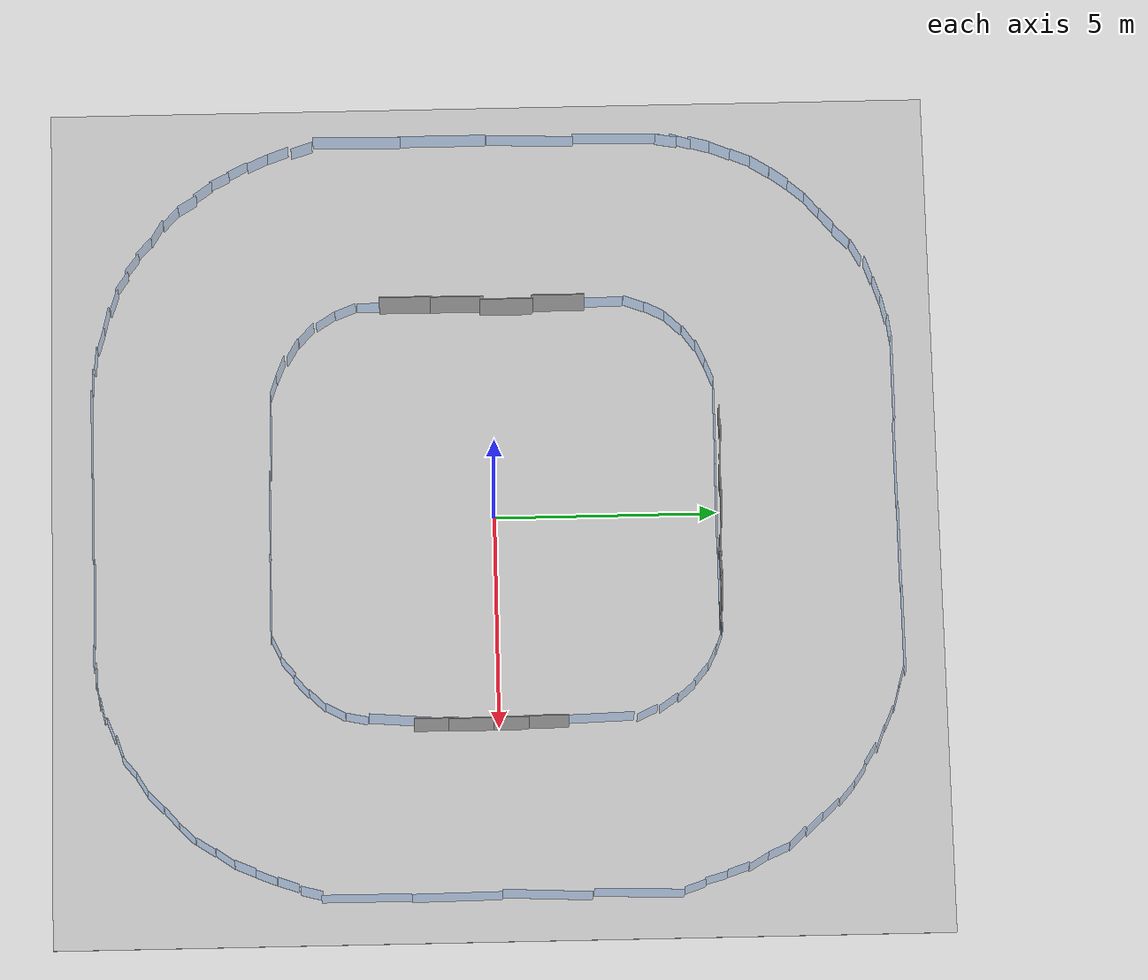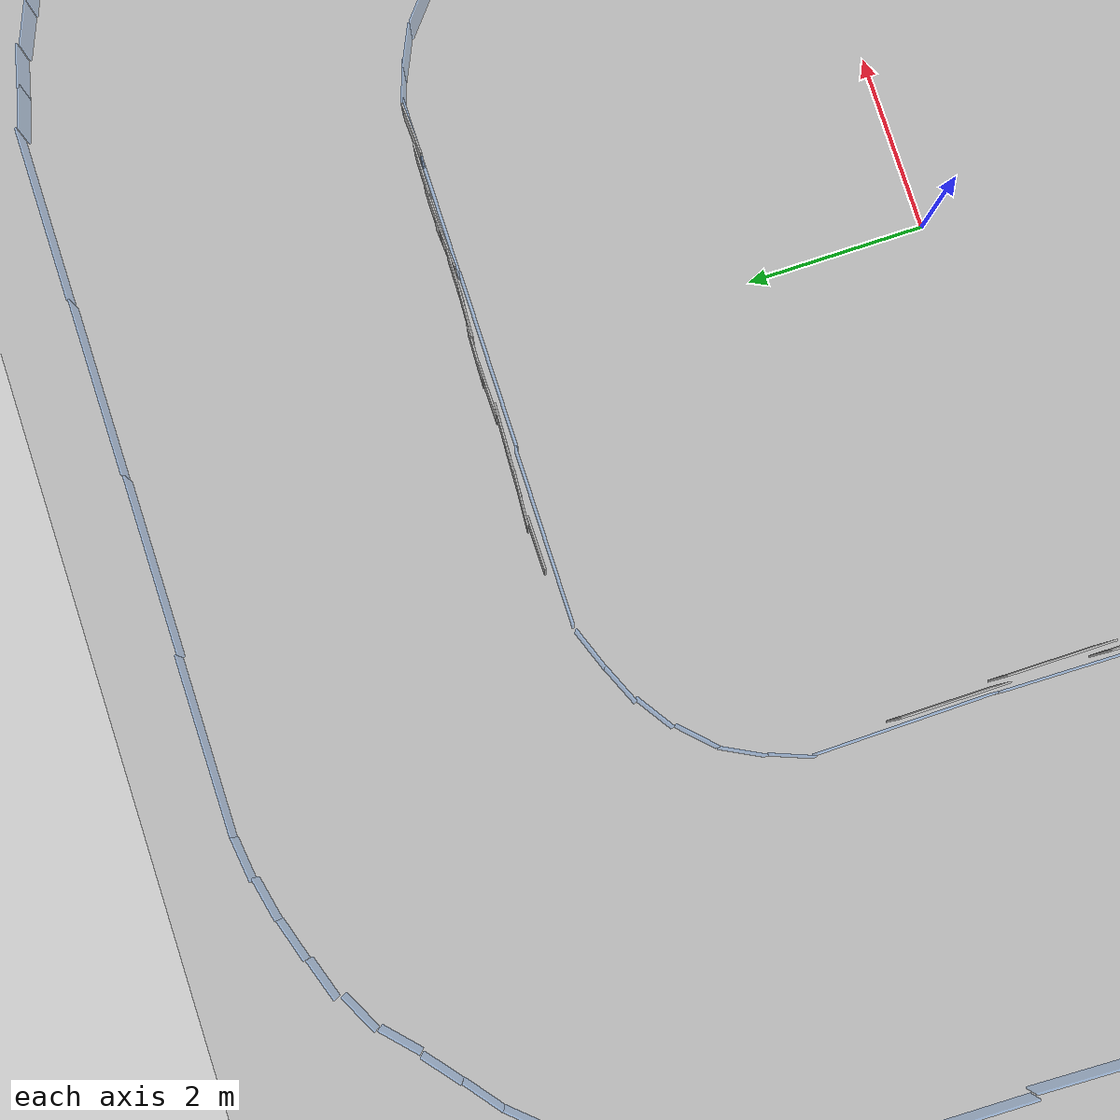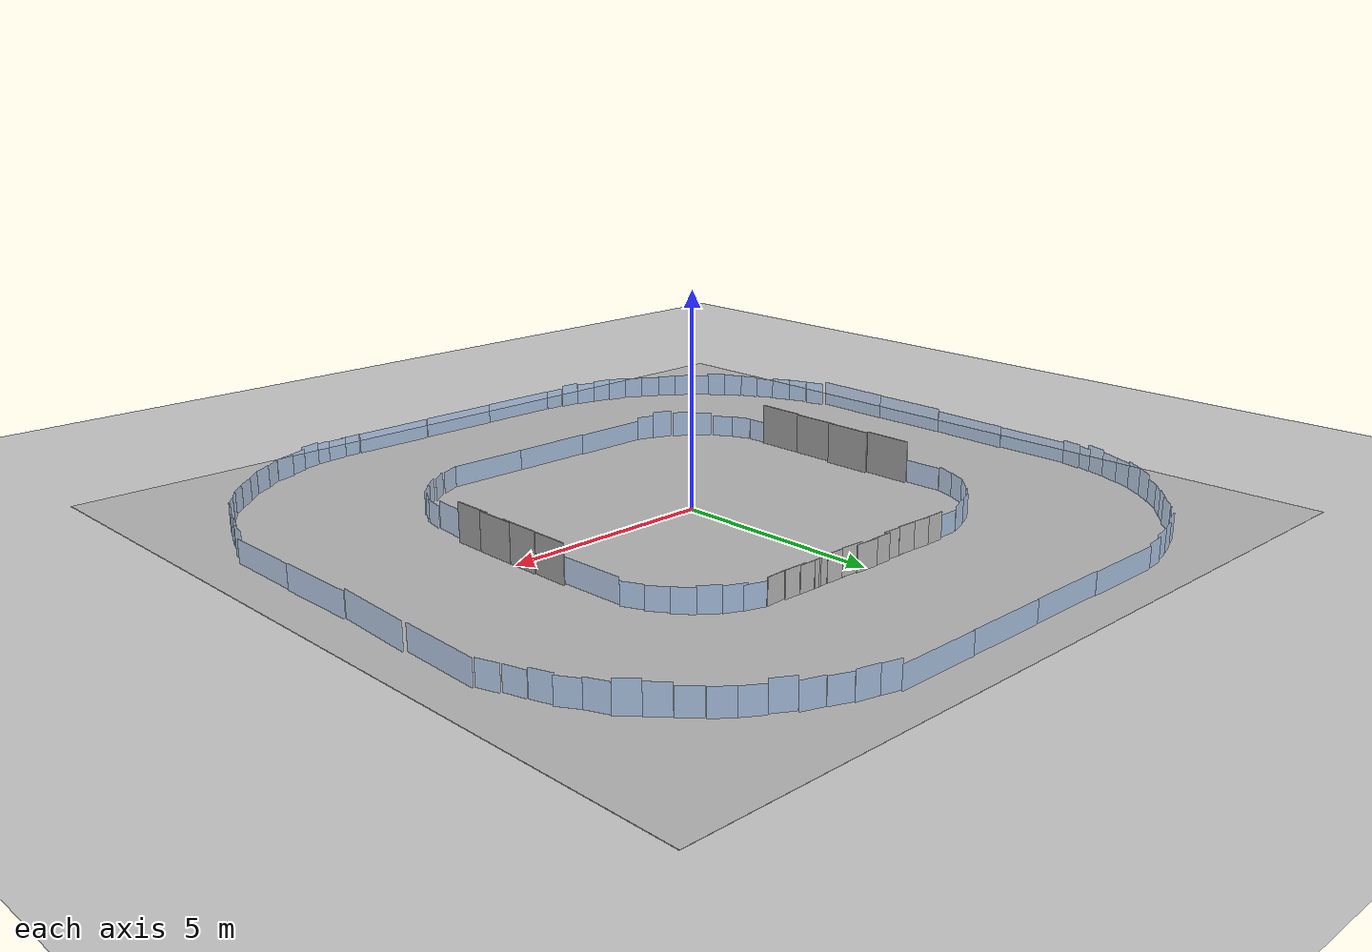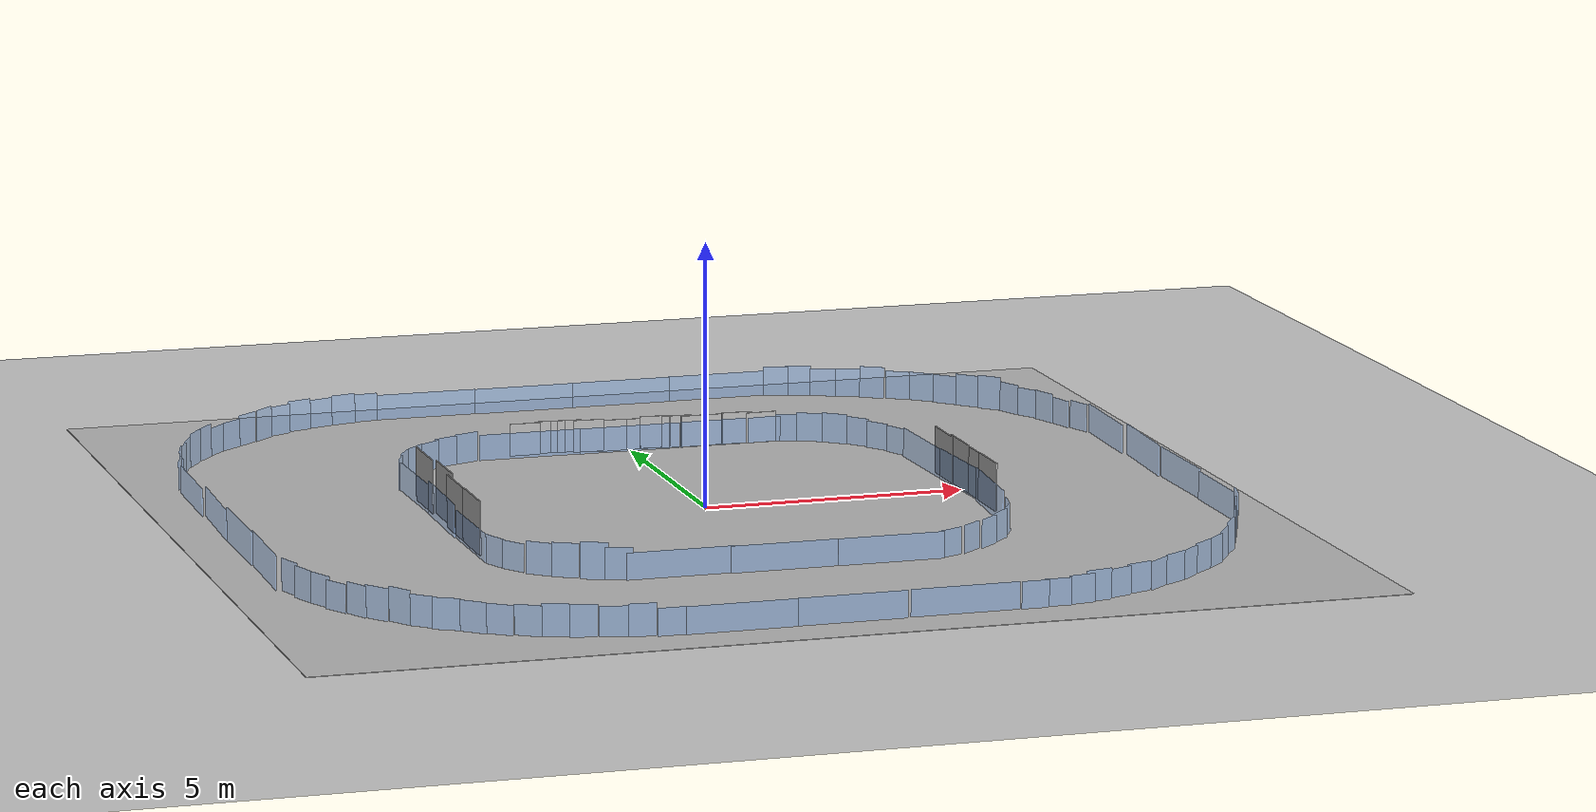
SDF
<sdf version="1.7">
 <world name="saft_city_arena">
  <physics type="ode">
   <real_time_update_rate>500</real_time_update_rate>
   <max_step_size>0.002</max_step_size>
   <real_time_factor>1</real_time_factor>
  </physics>
  <light name="sun" type="directional">
   <pose>0 0 10 0 -0 0</pose>
   <diffuse>0.8 0.8 0.8 1</diffuse>
   <specular>0.2 0.2 0.2 1</specular>
   <attenuation>
    <range>1000</range>
    <constant>0.9</constant>
    <linear>0.01</linear>
    <quadratic>0.001</quadratic>
   </attenuation>
   <direction>-0.5 0.1 -0.9</direction>
   <spot><inner_angle>0</inner_angle><outer_angle>0</outer_angle><falloff>0</falloff></spot>
  </light>
  <model name="ground_plane">
   <static>1</static>
   <link name="link">
    <collision name="collision">
     <geometry><plane><normal>0 0 1</normal><size>100 100</size></plane></geometry>
     <surface>
      <contact><collide_bitmask>65535</collide_bitmask></contact>
      <friction><ode><mu>100</mu><mu2>50</mu2></ode></friction>
     </surface>
    </collision>
    <visual name="visual">
     <cast_shadows>0</cast_shadows>
     <geometry><plane><normal>0 0 1</normal><size>100 100</size></plane></geometry>
     <material>
      <script><uri>file://media/materials/scripts/gazebo.material</uri><name>Gazebo/Grey</name></script>
     </material>
    </visual>
   </link>
  </model>
  <model name="race_track">
   <pose>-0.01892 0.017455 0 0 -0 0</pose>
   <static>1</static>
   <link name="ground">
    <collision name="collision">
     <pose>0 0 -0.025 0 -0 0</pose>
     <geometry><box><size>20 20 0.08</size></box></geometry>
    </collision>
    <visual name="visual">
     <pose>0 0 0.005 0 -0 0</pose>
     <geometry><box><size>20 20 0.01</size></box></geometry>
     <material><script><uri>model://race_track</uri><name>race_track/ground</name></script></material>
    </visual>
   </link>
  </model>
  <gravity>0 0 -9.8</gravity>
  <magnetic_field>6e-06 2.3e-05 -4.2e-05</magnetic_field>
  <atmosphere type="adiabatic"/>
  <scene><ambient>0.4 0.4 0.4 1</ambient><background>0.7 0.7 0.7 1</background><shadows>1</shadows></scene>
  <spherical_coordinates>
   <surface_model>EARTH_WGS84</surface_model>
   <latitude_deg>0</latitude_deg>
   <longitude_deg>0</longitude_deg>
   <elevation>0</elevation>
   <heading_deg>0</heading_deg>
  </spherical_coordinates>
  <model name="trash_sign_01">
   <static>1</static>
   <link name="sign">
    <visual name="visual">
     <pose>0 0 0.1 0 -0 0</pose>
     <geometry><box><size>0.02 1 1</size></box></geometry>
     <material>
      <script>
       <uri>model://photo_signs/trash_sign_01/materials/scripts</uri>
       <uri>model://photo_signs/trash_sign_01/materials/textures</uri>
       <name>PhotoSign/trash_sign_01</name>
      </script>
     </material>
    </visual>
   </link>
   <pose>5.03179 -1.40382 0.327227 0 -0 0</pose>
  </model>
  <model name="trash_sign_02">
   <static>1</static>
   <link name="sign">
    <visual name="visual">
     <pose>0 0 0.1 0 -0 0</pose>
     <geometry><box><size>0.02 1 1</size></box></geometry>
     <material>
      <script>
       <uri>model://photo_signs/trash_sign_02/materials/scripts</uri>
       <uri>model://photo_signs/trash_sign_02/materials/textures</uri>
       <name>PhotoSign/trash_sign_02</name>
      </script>
     </material>
    </visual>
   </link>
   <pose>5.04017 -0.636448 0.309953 0 -0 0</pose>
  </model>
  <model name="trash_sign_03">
   <static>1</static>
   <link name="sign">
    <visual name="visual">
     <pose>0 0 0.1 0 -0 0</pose>
     <geometry><box><size>0.02 1 1</size></box></geometry>
     <material>
      <script>
       <uri>model://photo_signs/trash_sign_03/materials/scripts</uri>
       <uri>model://photo_signs/trash_sign_03/materials/textures</uri>
       <name>PhotoSign/trash_sign_03</name>
      </script>
     </material>
    </visual>
   </link>
   <pose>5.03698 0.168034 0.324503 0 -0 0</pose>
  </model>
  <model name="trash_sign_04">
   <static>1</static>
   <link name="sign">
    <visual name="visual">
     <pose>0 0 0.1 0 -0 0</pose>
     <geometry><box><size>0.02 1 1</size></box></geometry>
     <material>
      <script>
       <uri>model://photo_signs/trash_sign_04/materials/scripts</uri>
       <uri>model://photo_signs/trash_sign_04/materials/textures</uri>
       <name>PhotoSign/trash_sign_04</name>
      </script>
     </material>
    </visual>
   </link>
   <pose>5.01136 1.04539 0.304628 0 -0 0</pose>
  </model>
  <model name="building_sign_01">
   <static>1</static>
   <link name="sign">
    <visual name="visual">
     <pose>0 0 0.175 0 -0 0</pose>
     <geometry><box><size>0.02 1.2 1.2</size></box></geometry>
     <material>
      <script>
       <uri>model://photo_signs/building_sign_01/materials/scripts</uri>
       <uri>model://photo_signs/building_sign_01/materials/textures</uri>
       <name>PhotoSign/building_sign_01</name>
      </script>
     </material>
    </visual>
   </link>
   <pose>-4.98428 1.54626 0.247239 0 -0 0</pose>
  </model>
  <model name="building_sign_02">
   <static>1</static>
   <link name="sign">
    <visual name="visual">
     <pose>0 0 0.175 0 -0 0</pose>
     <geometry><box><size>0.02 1.2 1.2</size></box></geometry>
     <material>
      <script>
       <uri>model://photo_signs/building_sign_02/materials/scripts</uri>
       <uri>model://photo_signs/building_sign_02/materials/textures</uri>
       <name>PhotoSign/building_sign_02</name>
      </script>
     </material>
    </visual>
   </link>
   <pose>-4.91211 0.369082 0.244687 0 -0 0</pose>
  </model>
  <model name="building_sign_03">
   <static>1</static>
   <link name="sign">
    <visual name="visual">
     <pose>0 0 0.175 0 -0 0</pose>
     <geometry><box><size>0.02 1.2 1.2</size></box></geometry>
     <material>
      <script>
       <uri>model://photo_signs/building_sign_03/materials/scripts</uri>
       <uri>model://photo_signs/building_sign_03/materials/textures</uri>
       <name>PhotoSign/building_sign_03</name>
      </script>
     </material>
    </visual>
   </link>
   <pose>-4.99648 -0.747766 0.224309 0 -0 0</pose>
  </model>
  <model name="building_sign_04">
   <static>1</static>
   <link name="sign">
    <visual name="visual">
     <pose>0 0 0.175 0 -0 0</pose>
     <geometry><box><size>0.02 1.2 1.2</size></box></geometry>
     <material>
      <script>
       <uri>model://photo_signs/building_sign_04/materials/scripts</uri>
       <uri>model://photo_signs/building_sign_04/materials/textures</uri>
       <name>PhotoSign/building_sign_04</name>
      </script>
     </material>
    </visual>
   </link>
   <pose>-5.00213 -1.91043 0.243349 0 -0 0</pose>
  </model>
  <model name="person_sign_01">
   <static>1</static>
   <link name="sign">
    <visual name="visual">
     <pose>0 0 0.16 0 -0 0</pose>
     <geometry><box><size>0.02 0.6 0.62</size></box></geometry>
     <material>
      <script>
       <uri>model://photo_signs/person_sign_01/materials/scripts</uri>
       <uri>model://photo_signs/person_sign_01/materials/textures</uri>
       <name>PhotoSign/person_sign_01</name>
      </script>
     </material>
    </visual>
   </link>
   <pose>2.14956 5.05182 0.150774 0 0 -1.58447</pose>
  </model>
  <model name="person_sign_02">
   <static>1</static>
   <link name="sign">
    <visual name="visual">
     <pose>0 0 0.16 0 -0 0</pose>
     <geometry><box><size>0.02 0.6 0.62</size></box></geometry>
     <material>
      <script>
       <uri>model://photo_signs/person_sign_02/materials/scripts</uri>
       <uri>model://photo_signs/person_sign_02/materials/textures</uri>
       <name>PhotoSign/person_sign_02</name>
      </script>
     </material>
    </visual>
   </link>
   <pose>1.73394 5.06385 0.137015 0 0 -1.56904</pose>
  </model>
  <model name="person_sign_03">
   <static>1</static>
   <link name="sign">
    <visual name="visual">
     <pose>0 0 0.16 0 -0 0</pose>
     <geometry><box><size>0.02 0.6 0.62</size></box></geometry>
     <material>
      <script>
       <uri>model://photo_signs/person_sign_03/materials/scripts</uri>
       <uri>model://photo_signs/person_sign_03/materials/textures</uri>
       <name>PhotoSign/person_sign_03</name>
      </script>
     </material>
    </visual>
   </link>
   <pose>1.32292 5.05339 0.139864 0 0 -1.50844</pose>
  </model>
  <model name="person_sign_04">
   <static>1</static>
   <link name="sign">
    <visual name="visual">
     <pose>0 0 0.16 0 -0 0</pose>
     <geometry><box><size>0.02 0.6 0.62</size></box></geometry>
     <material>
      <script>
       <uri>model://photo_signs/person_sign_04/materials/scripts</uri>
       <uri>model://photo_signs/person_sign_04/materials/textures</uri>
       <name>PhotoSign/person_sign_04</name>
      </script>
     </material>
    </visual>
   </link>
   <pose>0.931752 5.06364 0.158173 0 0 -1.58189</pose>
  </model>
  <model name="person_sign_05">
   <static>1</static>
   <link name="sign">
    <visual name="visual">
     <pose>0 0 0.16 0 -0 0</pose>
     <geometry><box><size>0.02 0.6 0.62</size></box></geometry>
     <material>
      <script>
       <uri>model://photo_signs/person_sign_05/materials/scripts</uri>
       <uri>model://photo_signs/person_sign_05/materials/textures</uri>
       <name>PhotoSign/person_sign_05</name>
      </script>
     </material>
    </visual>
   </link>
   <pose>0.515768 5.07932 0.173126 0 0 -1.62224</pose>
  </model>
  <model name="person_sign_06">
   <static>1</static>
   <link name="sign">
    <visual name="visual">
     <pose>0 0 0.16 0 -0 0</pose>
     <geometry><box><size>0.02 0.6 0.62</size></box></geometry>
     <material>
      <script>
       <uri>model://photo_signs/person_sign_06/materials/scripts</uri>
       <uri>model://photo_signs/person_sign_06/materials/textures</uri>
       <name>PhotoSign/person_sign_06</name>
      </script>
     </material>
    </visual>
   </link>
   <pose>0.071031 5.11301 0.138445 0 0 -1.6041</pose>
  </model>
  <model name="person_sign_07">
   <static>1</static>
   <link name="sign">
    <visual name="visual">
     <pose>0 0 0.16 0 -0 0</pose>
     <geometry><box><size>0.02 0.6 0.62</size></box></geometry>
     <material>
      <script>
       <uri>model://photo_signs/person_sign_07/materials/scripts</uri>
       <uri>model://photo_signs/person_sign_07/materials/textures</uri>
       <name>PhotoSign/person_sign_07</name>
      </script>
     </material>
    </visual>
   </link>
   <pose>-0.349251 5.10924 0.145721 0 0 -1.55728</pose>
  </model>
  <model name="person_sign_08">
   <static>1</static>
   <link name="sign">
    <visual name="visual">
     <pose>0 0 0.16 0 -0 0</pose>
     <geometry><box><size>0.02 0.6 0.62</size></box></geometry>
     <material>
      <script>
       <uri>model://photo_signs/person_sign_08/materials/scripts</uri>
       <uri>model://photo_signs/person_sign_08/materials/textures</uri>
       <name>PhotoSign/person_sign_08</name>
      </script>
     </material>
    </visual>
   </link>
   <pose>-0.820761 5.0966 0.177459 0 0 -1.60914</pose>
  </model>
  <model name="person_sign_09">
   <static>1</static>
   <link name="sign">
    <visual name="visual">
     <pose>0 0 0.16 0 -0 0</pose>
     <geometry><box><size>0.02 0.6 0.62</size></box></geometry>
     <material>
      <script>
       <uri>model://photo_signs/person_sign_09/materials/scripts</uri>
       <uri>model://photo_signs/person_sign_09/materials/textures</uri>
       <name>PhotoSign/person_sign_09</name>
      </script>
     </material>
    </visual>
   </link>
   <pose>-1.26214 5.11592 0.19236 0 0 -1.6064</pose>
  </model>
  <model name="person_sign_10">
   <static>1</static>
   <link name="sign">
    <visual name="visual">
     <pose>0 0 0.16 0 -0 0</pose>
     <geometry><box><size>0.02 0.6 0.62</size></box></geometry>
     <material>
      <script>
       <uri>model://photo_signs/person_sign_10/materials/scripts</uri>
       <uri>model://photo_signs/person_sign_10/materials/textures</uri>
       <name>PhotoSign/person_sign_10</name>
      </script>
     </material>
    </visual>
   </link>
   <pose>-1.58387 5.13215 0.194342 0 0 -1.63895</pose>
  </model>
  <model name="person_sign_11">
   <static>1</static>
   <link name="sign">
    <visual name="visual">
     <pose>0 0 0.16 0 -0 0</pose>
     <geometry><box><size>0.02 0.6 0.62</size></box></geometry>
     <material>
      <script>
       <uri>model://photo_signs/person_sign_11/materials/scripts</uri>
       <uri>model://photo_signs/person_sign_11/materials/textures</uri>
       <name>PhotoSign/person_sign_11</name>
      </script>
     </material>
    </visual>
   </link>
   <pose>-2.07522 5.12272 0.182686 0 0 -1.56299</pose>
  </model>
  <model name="person_sign_12">
   <static>1</static>
   <link name="sign">
    <visual name="visual">
     <pose>0 0 0.16 0 -0 0</pose>
     <geometry><box><size>0.02 0.6 0.62</size></box></geometry>
     <material>
      <script>
       <uri>model://photo_signs/person_sign_12/materials/scripts</uri>
       <uri>model://photo_signs/person_sign_12/materials/textures</uri>
       <name>PhotoSign/person_sign_12</name>
      </script>
     </material>
    </visual>
   </link>
   <pose>2.62259 5.01801 0.129118 0 0 -1.52126</pose>
  </model>
  <model name="transparent_wall">
   <static>1</static>
   <link name="wall">
    <collision name="collision"><geometry><box><size>2 0.02 1</size></box></geometry></collision>
    <visual name="visual">
     <geometry><box><size>2 0.02 1</size></box></geometry>
     <material>
      <ambient>0.3 0.6 1 0.3</ambient>
      <diffuse>0.3 0.6 1 0.3</diffuse>
      <specular>0 0 0 0</specular>
      <emissive>0 0 0 0</emissive>
     </material>
    </visual>
   </link>
   <pose>-0.063638 -5.05574 0 0 -0 0</pose>
  </model>
  <model name="transparent_wall_0">
   <static>1</static>
   <link name="wall">
    <collision name="collision"><geometry><box><size>2 0.02 1</size></box></geometry></collision>
    <visual name="visual">
     <geometry><box><size>2 0.02 1</size></box></geometry>
     <material>
      <ambient>0.3 0.6 1 0.3</ambient>
      <diffuse>0.3 0.6 1 0.3</diffuse>
      <specular>0 0 0 0</specular>
      <emissive>0 0 0 0</emissive>
     </material>
    </visual>
   </link>
   <pose>-1.98522 -5.01412 0 0 -0 0</pose>
  </model>
  <model name="transparent_wall_1">
   <static>1</static>
   <link name="wall">
    <collision name="collision"><geometry><box><size>2 0.02 1</size></box></geometry></collision>
    <visual name="visual">
     <geometry><box><size>2 0.02 1</size></box></geometry>
     <material>
      <ambient>0.3 0.6 1 0.3</ambient>
      <diffuse>0.3 0.6 1 0.3</diffuse>
      <specular>0 0 0 0</specular>
      <emissive>0 0 0 0</emissive>
     </material>
    </visual>
   </link>
   <pose>-2.09189 -9.06095 0 0 -0 0</pose>
  </model>
  <model name="transparent_wall_2">
   <static>1</static>
   <link name="wall">
    <collision name="collision"><geometry><box><size>2 0.02 1</size></box></geometry></collision>
    <visual name="visual">
     <geometry><box><size>2 0.02 1</size></box></geometry>
     <material>
      <ambient>0.3 0.6 1 0.3</ambient>
      <diffuse>0.3 0.6 1 0.3</diffuse>
      <specular>0 0 0 0</specular>
      <emissive>0 0 0 0</emissive>
     </material>
    </visual>
   </link>
   <pose>-0.079167 -9.04363 0 0 -0 0</pose>
  </model>
  <model name="transparent_wall_3">
   <static>1</static>
   <link name="wall">
    <collision name="collision"><geometry><box><size>2 0.02 1</size></box></geometry></collision>
    <visual name="visual">
     <geometry><box><size>2 0.02 1</size></box></geometry>
     <material>
      <ambient>0.3 0.6 1 0.3</ambient>
      <diffuse>0.3 0.6 1 0.3</diffuse>
      <specular>0 0 0 0</specular>
      <emissive>0 0 0 0</emissive>
     </material>
    </visual>
   </link>
   <pose>1.97662 -9.01296 0 0 -0 0</pose>
  </model>
  <model name="transparent_wall_4">
   <static>1</static>
   <link name="wall">
    <collision name="collision"><geometry><box><size>2 0.02 1</size></box></geometry></collision>
    <visual name="visual">
     <geometry><box><size>2 0.02 1</size></box></geometry>
     <material>
      <ambient>0.3 0.6 1 0.3</ambient>
      <diffuse>0.3 0.6 1 0.3</diffuse>
      <specular>0 0 0 0</specular>
      <emissive>0 0 0 0</emissive>
     </material>
    </visual>
   </link>
   <pose>1.93743 -5.06455 0 0 -0 0</pose>
  </model>
  <model name="transparent_wall_5">
   <static>1</static>
   <link name="wall">
    <collision name="collision"><geometry><box><size>2 0.02 1</size></box></geometry></collision>
    <visual name="visual">
     <geometry><box><size>2 0.02 1</size></box></geometry>
     <material>
      <ambient>0.3 0.6 1 0.3</ambient>
      <diffuse>0.3 0.6 1 0.3</diffuse>
      <specular>0 0 0 0</specular>
      <emissive>0 0 0 0</emissive>
     </material>
    </visual>
   </link>
   <pose>-5.05108 -2.0249 0.028425 0 0 -1.56328</pose>
  </model>
  <model name="transparent_wall_6">
   <static>1</static>
   <link name="wall">
    <collision name="collision"><geometry><box><size>2 0.02 1</size></box></geometry></collision>
    <visual name="visual">
     <geometry><box><size>2 0.02 1</size></box></geometry>
     <material>
      <ambient>0.3 0.6 1 0.3</ambient>
      <diffuse>0.3 0.6 1 0.3</diffuse>
      <specular>0 0 0 0</specular>
      <emissive>0 0 0 0</emissive>
     </material>
    </visual>
   </link>
   <pose>-5.07219 -0.024101 0.128366 0 -0 1.55488</pose>
  </model>
  <model name="transparent_wall_7">
   <static>1</static>
   <link name="wall">
    <collision name="collision"><geometry><box><size>2 0.02 1</size></box></geometry></collision>
    <visual name="visual">
     <geometry><box><size>2 0.02 1</size></box></geometry>
     <material>
      <ambient>0.3 0.6 1 0.3</ambient>
      <diffuse>0.3 0.6 1 0.3</diffuse>
      <specular>0 0 0 0</specular>
      <emissive>0 0 0 0</emissive>
     </material>
    </visual>
   </link>
   <pose>-5.06249 2.00981 0.041984 0 -0 1.58519</pose>
  </model>
  <model name="transparent_wall_8">
   <static>1</static>
   <link name="wall">
    <collision name="collision"><geometry><box><size>2 0.02 1</size></box></geometry></collision>
    <visual name="visual">
     <geometry><box><size>2 0.02 1</size></box></geometry>
     <material>
      <ambient>0.3 0.6 1 0.3</ambient>
      <diffuse>0.3 0.6 1 0.3</diffuse>
      <specular>0 0 0 0</specular>
      <emissive>0 0 0 0</emissive>
     </material>
    </visual>
   </link>
   <pose>4.8982 -1.90916 0.141159 0 0 -1.65353</pose>
  </model>
  <model name="transparent_wall_9">
   <static>1</static>
   <link name="wall">
    <collision name="collision"><geometry><box><size>2 0.02 1</size></box></geometry></collision>
    <visual name="visual">
     <geometry><box><size>2 0.02 1</size></box></geometry>
     <material>
      <ambient>0.3 0.6 1 0.3</ambient>
      <diffuse>0.3 0.6 1 0.3</diffuse>
      <specular>0 0 0 0</specular>
      <emissive>0 0 0 0</emissive>
     </material>
    </visual>
   </link>
   <pose>4.98103 0.003821 0.088769 0 0 -1.51702</pose>
  </model>
  <model name="transparent_wall_10">
   <static>1</static>
   <link name="wall">
    <collision name="collision"><geometry><box><size>2 0.02 1</size></box></geometry></collision>
    <visual name="visual">
     <geometry><box><size>2 0.02 1</size></box></geometry>
     <material>
      <ambient>0.3 0.6 1 0.3</ambient>
      <diffuse>0.3 0.6 1 0.3</diffuse>
      <specular>0 0 0 0</specular>
      <emissive>0 0 0 0</emissive>
     </material>
    </visual>
   </link>
   <pose>4.90263 2.00371 0.067201 0 -0 1.60296</pose>
  </model>
  <model name="transparent_wall_11">
   <static>1</static>
   <link name="wall">
    <collision name="collision"><geometry><box><size>2 0.02 1</size></box></geometry></collision>
    <visual name="visual">
     <geometry><box><size>2 0.02 1</size></box></geometry>
     <material>
      <ambient>0.3 0.6 1 0.3</ambient>
      <diffuse>0.3 0.6 1 0.3</diffuse>
      <specular>0 0 0 0</specular>
      <emissive>0 0 0 0</emissive>
     </material>
    </visual>
   </link>
   <pose>2.00706 5.00496 0 0 -0 0</pose>
  </model>
  <model name="transparent_wall_12">
   <static>1</static>
   <link name="wall">
    <collision name="collision"><geometry><box><size>2 0.02 1</size></box></geometry></collision>
    <visual name="visual">
     <geometry><box><size>2 0.02 1</size></box></geometry>
     <material>
      <ambient>0.3 0.6 1 0.3</ambient>
      <diffuse>0.3 0.6 1 0.3</diffuse>
      <specular>0 0 0 0</specular>
      <emissive>0 0 0 0</emissive>
     </material>
    </visual>
   </link>
   <pose>-0.012906 4.99693 0 0 -0 0</pose>
  </model>
  <model name="transparent_wall_13">
   <static>1</static>
   <link name="wall">
    <collision name="collision"><geometry><box><size>2 0.02 1</size></box></geometry></collision>
    <visual name="visual">
     <geometry><box><size>2 0.02 1</size></box></geometry>
     <material>
      <ambient>0.3 0.6 1 0.3</ambient>
      <diffuse>0.3 0.6 1 0.3</diffuse>
      <specular>0 0 0 0</specular>
      <emissive>0 0 0 0</emissive>
     </material>
    </visual>
   </link>
   <pose>-2.00866 5.01257 0 0 -0 0</pose>
  </model>
  <model name="transparent_wall_short">
   <static>1</static>
   <link name="wall">
    <collision name="collision"><geometry><box><size>0.5 0.02 1</size></box></geometry></collision>
    <visual name="visual">
     <geometry><box><size>0.5 0.02 1</size></box></geometry>
     <material>
      <ambient>0.3 0.6 1 0.3</ambient>
      <diffuse>0.3 0.6 1 0.3</diffuse>
      <specular>0 0 0 0</specular>
      <emissive>0 0 0 0</emissive>
     </material>
    </visual>
   </link>
   <pose>-4.94708 -3.28797 0.040987 0 0 -1.18648</pose>
  </model>
  <model name="transparent_wall_short_0">
   <static>1</static>
   <link name="wall">
    <collision name="collision"><geometry><box><size>0.5 0.02 1</size></box></geometry></collision>
    <visual name="visual">
     <geometry><box><size>0.5 0.02 1</size></box></geometry>
     <material>
      <ambient>0.3 0.6 1 0.3</ambient>
      <diffuse>0.3 0.6 1 0.3</diffuse>
      <specular>0 0 0 0</specular>
      <emissive>0 0 0 0</emissive>
     </material>
    </visual>
   </link>
   <pose>-4.7203 -3.73547 0.029213 0 0 -0.987347</pose>
  </model>
  <model name="transparent_wall_short_1">
   <static>1</static>
   <link name="wall">
    <collision name="collision"><geometry><box><size>0.5 0.02 1</size></box></geometry></collision>
    <visual name="visual">
     <geometry><box><size>0.5 0.02 1</size></box></geometry>
     <material>
      <ambient>0.3 0.6 1 0.3</ambient>
      <diffuse>0.3 0.6 1 0.3</diffuse>
      <specular>0 0 0 0</specular>
      <emissive>0 0 0 0</emissive>
     </material>
    </visual>
   </link>
   <pose>-4.37851 -4.17919 0.107006 0 0 -0.722057</pose>
  </model>
  <model name="transparent_wall_short_2">
   <static>1</static>
   <link name="wall">
    <collision name="collision"><geometry><box><size>0.5 0.02 1</size></box></geometry></collision>
    <visual name="visual">
     <geometry><box><size>0.5 0.02 1</size></box></geometry>
     <material>
      <ambient>0.3 0.6 1 0.3</ambient>
      <diffuse>0.3 0.6 1 0.3</diffuse>
      <specular>0 0 0 0</specular>
      <emissive>0 0 0 0</emissive>
     </material>
    </visual>
   </link>
   <pose>-3.96842 -4.49368 0.136805 0 0 -0.518828</pose>
  </model>
  <model name="transparent_wall_short_3">
   <static>1</static>
   <link name="wall">
    <collision name="collision"><geometry><box><size>0.5 0.02 1</size></box></geometry></collision>
    <visual name="visual">
     <geometry><box><size>0.5 0.02 1</size></box></geometry>
     <material>
      <ambient>0.3 0.6 1 0.3</ambient>
      <diffuse>0.3 0.6 1 0.3</diffuse>
      <specular>0 0 0 0</specular>
      <emissive>0 0 0 0</emissive>
     </material>
    </visual>
   </link>
   <pose>-3.51803 -4.77775 0.183505 0 0 -0.369282</pose>
  </model>
  <model name="transparent_wall_short_4">
   <static>1</static>
   <link name="wall">
    <collision name="collision"><geometry><box><size>0.5 0.02 1</size></box></geometry></collision>
    <visual name="visual">
     <geometry><box><size>0.5 0.02 1</size></box></geometry>
     <material>
      <ambient>0.3 0.6 1 0.3</ambient>
      <diffuse>0.3 0.6 1 0.3</diffuse>
      <specular>0 0 0 0</specular>
      <emissive>0 0 0 0</emissive>
     </material>
    </visual>
   </link>
   <pose>-3.10991 -4.93677 0.093668 0 0 -0.308535</pose>
  </model>
  <model name="transparent_wall_short_5">
   <static>1</static>
   <link name="wall">
    <collision name="collision"><geometry><box><size>0.5 0.02 1</size></box></geometry></collision>
    <visual name="visual">
     <geometry><box><size>0.5 0.02 1</size></box></geometry>
     <material>
      <ambient>0.3 0.6 1 0.3</ambient>
      <diffuse>0.3 0.6 1 0.3</diffuse>
      <specular>0 0 0 0</specular>
      <emissive>0 0 0 0</emissive>
     </material>
    </visual>
   </link>
   <pose>3.11225 -4.94553 0.008288 0 -0 0.440215</pose>
  </model>
  <model name="transparent_wall_short_6">
   <static>1</static>
   <link name="wall">
    <collision name="collision"><geometry><box><size>0.5 0.02 1</size></box></geometry></collision>
    <visual name="visual">
     <geometry><box><size>0.5 0.02 1</size></box></geometry>
     <material>
      <ambient>0.3 0.6 1 0.3</ambient>
      <diffuse>0.3 0.6 1 0.3</diffuse>
      <specular>0 0 0 0</specular>
      <emissive>0 0 0 0</emissive>
     </material>
    </visual>
   </link>
   <pose>3.58736 -4.68834 0.024846 0 -0 0.688681</pose>
  </model>
  <model name="transparent_wall_short_7">
   <static>1</static>
   <link name="wall">
    <collision name="collision"><geometry><box><size>0.5 0.02 1</size></box></geometry></collision>
    <visual name="visual">
     <geometry><box><size>0.5 0.02 1</size></box></geometry>
     <material>
      <ambient>0.3 0.6 1 0.3</ambient>
      <diffuse>0.3 0.6 1 0.3</diffuse>
      <specular>0 0 0 0</specular>
      <emissive>0 0 0 0</emissive>
     </material>
    </visual>
   </link>
   <pose>4.02029 -4.40085 0.035984 0 -0 0.715586</pose>
  </model>
  <model name="transparent_wall_short_8">
   <static>1</static>
   <link name="wall">
    <collision name="collision"><geometry><box><size>0.5 0.02 1</size></box></geometry></collision>
    <visual name="visual">
     <geometry><box><size>0.5 0.02 1</size></box></geometry>
     <material>
      <ambient>0.3 0.6 1 0.3</ambient>
      <diffuse>0.3 0.6 1 0.3</diffuse>
      <specular>0 0 0 0</specular>
      <emissive>0 0 0 0</emissive>
     </material>
    </visual>
   </link>
   <pose>4.36224 -4.04912 0.049637 0 -0 0.783063</pose>
  </model>
  <model name="transparent_wall_short_9">
   <static>1</static>
   <link name="wall">
    <collision name="collision"><geometry><box><size>0.5 0.02 1</size></box></geometry></collision>
    <visual name="visual">
     <geometry><box><size>0.5 0.02 1</size></box></geometry>
     <material>
      <ambient>0.3 0.6 1 0.3</ambient>
      <diffuse>0.3 0.6 1 0.3</diffuse>
      <specular>0 0 0 0</specular>
      <emissive>0 0 0 0</emissive>
     </material>
    </visual>
   </link>
   <pose>4.63881 -3.651 0.033295 -0.016287 -0.009075 1.06248</pose>
  </model>
  <model name="transparent_wall_short_10">
   <static>1</static>
   <link name="wall">
    <collision name="collision"><geometry><box><size>0.5 0.02 1</size></box></geometry></collision>
    <visual name="visual">
     <geometry><box><size>0.5 0.02 1</size></box></geometry>
     <material>
      <ambient>0.3 0.6 1 0.3</ambient>
      <diffuse>0.3 0.6 1 0.3</diffuse>
      <specular>0 0 0 0</specular>
      <emissive>0 0 0 0</emissive>
     </material>
    </visual>
   </link>
   <pose>4.80251 -3.16733 0.029548 0 -0 1.36219</pose>
  </model>
  <model name="transparent_wall_short_11">
   <static>1</static>
   <link name="wall">
    <collision name="collision"><geometry><box><size>0.5 0.02 1</size></box></geometry></collision>
    <visual name="visual">
     <geometry><box><size>0.5 0.02 1</size></box></geometry>
     <material>
      <ambient>0.3 0.6 1 0.3</ambient>
      <diffuse>0.3 0.6 1 0.3</diffuse>
      <specular>0 0 0 0</specular>
      <emissive>0 0 0 0</emissive>
     </material>
    </visual>
   </link>
   <pose>4.80907 3.2971 0.020246 0 0 -1.12421</pose>
  </model>
  <model name="transparent_wall_short_12">
   <static>1</static>
   <link name="wall">
    <collision name="collision"><geometry><box><size>0.5 0.02 1</size></box></geometry></collision>
    <visual name="visual">
     <geometry><box><size>0.5 0.02 1</size></box></geometry>
     <material>
      <ambient>0.3 0.6 1 0.3</ambient>
      <diffuse>0.3 0.6 1 0.3</diffuse>
      <specular>0 0 0 0</specular>
      <emissive>0 0 0 0</emissive>
     </material>
    </visual>
   </link>
   <pose>4.58747 3.77696 0.026694 0 0 -0.949792</pose>
  </model>
  <model name="transparent_wall_short_13">
   <static>1</static>
   <link name="wall">
    <collision name="collision"><geometry><box><size>0.5 0.02 1</size></box></geometry></collision>
    <visual name="visual">
     <geometry><box><size>0.5 0.02 1</size></box></geometry>
     <material>
      <ambient>0.3 0.6 1 0.3</ambient>
      <diffuse>0.3 0.6 1 0.3</diffuse>
      <specular>0 0 0 0</specular>
      <emissive>0 0 0 0</emissive>
     </material>
    </visual>
   </link>
   <pose>4.32065 4.19695 0.051881 0 0 -0.856989</pose>
  </model>
  <model name="transparent_wall_short_14">
   <static>1</static>
   <link name="wall">
    <collision name="collision"><geometry><box><size>0.5 0.02 1</size></box></geometry></collision>
    <visual name="visual">
     <geometry><box><size>0.5 0.02 1</size></box></geometry>
     <material>
      <ambient>0.3 0.6 1 0.3</ambient>
      <diffuse>0.3 0.6 1 0.3</diffuse>
      <specular>0 0 0 0</specular>
      <emissive>0 0 0 0</emissive>
     </material>
    </visual>
   </link>
   <pose>3.96315 4.51815 0.08493 0 0 -0.687549</pose>
  </model>
  <model name="transparent_wall_short_15">
   <static>1</static>
   <link name="wall">
    <collision name="collision"><geometry><box><size>0.5 0.02 1</size></box></geometry></collision>
    <visual name="visual">
     <geometry><box><size>0.5 0.02 1</size></box></geometry>
     <material>
      <ambient>0.3 0.6 1 0.3</ambient>
      <diffuse>0.3 0.6 1 0.3</diffuse>
      <specular>0 0 0 0</specular>
      <emissive>0 0 0 0</emissive>
     </material>
    </visual>
   </link>
   <pose>3.54274 4.79572 0.065202 0 0 -0.429976</pose>
  </model>
  <model name="transparent_wall_short_16">
   <static>1</static>
   <link name="wall">
    <collision name="collision"><geometry><box><size>0.5 0.02 1</size></box></geometry></collision>
    <visual name="visual">
     <geometry><box><size>0.5 0.02 1</size></box></geometry>
     <material>
      <ambient>0.3 0.6 1 0.3</ambient>
      <diffuse>0.3 0.6 1 0.3</diffuse>
      <specular>0 0 0 0</specular>
      <emissive>0 0 0 0</emissive>
     </material>
    </visual>
   </link>
   <pose>3.17105 4.95409 0.02787 0 0 -0.324928</pose>
  </model>
  <model name="transparent_wall_short_17">
   <static>1</static>
   <link name="wall">
    <collision name="collision"><geometry><box><size>0.5 0.02 1</size></box></geometry></collision>
    <visual name="visual">
     <geometry><box><size>0.5 0.02 1</size></box></geometry>
     <material>
      <ambient>0.3 0.6 1 0.3</ambient>
      <diffuse>0.3 0.6 1 0.3</diffuse>
      <specular>0 0 0 0</specular>
      <emissive>0 0 0 0</emissive>
     </material>
    </visual>
   </link>
   <pose>-3.29522 4.91907 0.079268 0 -0 0.353213</pose>
  </model>
  <model name="transparent_wall_short_18">
   <static>1</static>
   <link name="wall">
    <collision name="collision"><geometry><box><size>0.5 0.02 1</size></box></geometry></collision>
    <visual name="visual">
     <geometry><box><size>0.5 0.02 1</size></box></geometry>
     <material>
      <ambient>0.3 0.6 1 0.3</ambient>
      <diffuse>0.3 0.6 1 0.3</diffuse>
      <specular>0 0 0 0</specular>
      <emissive>0 0 0 0</emissive>
     </material>
    </visual>
   </link>
   <pose>-3.74482 4.73577 0.064179 0 -0 0.407671</pose>
  </model>
  <model name="transparent_wall_short_19">
   <static>1</static>
   <link name="wall">
    <collision name="collision"><geometry><box><size>0.5 0.02 1</size></box></geometry></collision>
    <visual name="visual">
     <geometry><box><size>0.5 0.02 1</size></box></geometry>
     <material>
      <ambient>0.3 0.6 1 0.3</ambient>
      <diffuse>0.3 0.6 1 0.3</diffuse>
      <specular>0 0 0 0</specular>
      <emissive>0 0 0 0</emissive>
     </material>
    </visual>
   </link>
   <pose>-4.13752 4.4844 0.046875 0 -0 0.590745</pose>
  </model>
  <model name="transparent_wall_short_20">
   <static>1</static>
   <link name="wall">
    <collision name="collision"><geometry><box><size>0.5 0.02 1</size></box></geometry></collision>
    <visual name="visual">
     <geometry><box><size>0.5 0.02 1</size></box></geometry>
     <material>
      <ambient>0.3 0.6 1 0.3</ambient>
      <diffuse>0.3 0.6 1 0.3</diffuse>
      <specular>0 0 0 0</specular>
      <emissive>0 0 0 0</emissive>
     </material>
    </visual>
   </link>
   <pose>-4.50886 4.13866 0.064163 0 -0 0.783613</pose>
  </model>
  <model name="transparent_wall_short_21">
   <static>1</static>
   <link name="wall">
    <collision name="collision"><geometry><box><size>0.5 0.02 1</size></box></geometry></collision>
    <visual name="visual">
     <geometry><box><size>0.5 0.02 1</size></box></geometry>
     <material>
      <ambient>0.3 0.6 1 0.3</ambient>
      <diffuse>0.3 0.6 1 0.3</diffuse>
      <specular>0 0 0 0</specular>
      <emissive>0 0 0 0</emissive>
     </material>
    </visual>
   </link>
   <pose>-4.8132 3.72803 0.071165 0 -0 1.09326</pose>
  </model>
  <model name="transparent_wall_short_22">
   <static>1</static>
   <link name="wall">
    <collision name="collision"><geometry><box><size>0.5 0.02 1</size></box></geometry></collision>
    <visual name="visual">
     <geometry><box><size>0.5 0.02 1</size></box></geometry>
     <material>
      <ambient>0.3 0.6 1 0.3</ambient>
      <diffuse>0.3 0.6 1 0.3</diffuse>
      <specular>0 0 0 0</specular>
      <emissive>0 0 0 0</emissive>
     </material>
    </visual>
   </link>
   <pose>-5.00622 3.26337 0.071421 0 -0 1.20118</pose>
  </model>
  <model name="transparent_wall_14">
   <static>1</static>
   <link name="wall">
    <collision name="collision"><geometry><box><size>2 0.02 1</size></box></geometry></collision>
    <visual name="visual">
     <geometry><box><size>2 0.02 1</size></box></geometry>
     <material>
      <ambient>0.3 0.6 1 0.3</ambient>
      <diffuse>0.3 0.6 1 0.3</diffuse>
      <specular>0 0 0 0</specular>
      <emissive>0 0 0 0</emissive>
     </material>
    </visual>
   </link>
   <pose>-9.09276 -2.96726 0.139382 0 0 -1.59061</pose>
  </model>
  <model name="transparent_wall_15">
   <static>1</static>
   <link name="wall">
    <collision name="collision"><geometry><box><size>2 0.02 1</size></box></geometry></collision>
    <visual name="visual">
     <geometry><box><size>2 0.02 1</size></box></geometry>
     <material>
      <ambient>0.3 0.6 1 0.3</ambient>
      <diffuse>0.3 0.6 1 0.3</diffuse>
      <specular>0 0 0 0</specular>
      <emissive>0 0 0 0</emissive>
     </material>
    </visual>
   </link>
   <pose>-9.09233 -1.01612 0.12544 0 0 -1.57159</pose>
  </model>
  <model name="transparent_wall_16">
   <static>1</static>
   <link name="wall">
    <collision name="collision"><geometry><box><size>2 0.02 1</size></box></geometry></collision>
    <visual name="visual">
     <geometry><box><size>2 0.02 1</size></box></geometry>
     <material>
      <ambient>0.3 0.6 1 0.3</ambient>
      <diffuse>0.3 0.6 1 0.3</diffuse>
      <specular>0 0 0 0</specular>
      <emissive>0 0 0 0</emissive>
     </material>
    </visual>
   </link>
   <pose>-9.07089 0.997301 0.061654 0 0 -1.60555</pose>
  </model>
  <model name="transparent_wall_17">
   <static>1</static>
   <link name="wall">
    <collision name="collision"><geometry><box><size>2 0.02 1</size></box></geometry></collision>
    <visual name="visual">
     <geometry><box><size>2 0.02 1</size></box></geometry>
     <material>
      <ambient>0.3 0.6 1 0.3</ambient>
      <diffuse>0.3 0.6 1 0.3</diffuse>
      <specular>0 0 0 0</specular>
      <emissive>0 0 0 0</emissive>
     </material>
    </visual>
   </link>
   <pose>-9.08816 2.97502 0.023913 0 0 -1.58889</pose>
  </model>
  <model name="transparent_wall_18">
   <static>1</static>
   <link name="wall">
    <collision name="collision"><geometry><box><size>2 0.02 1</size></box></geometry></collision>
    <visual name="visual">
     <geometry><box><size>2 0.02 1</size></box></geometry>
     <material>
      <ambient>0.3 0.6 1 0.3</ambient>
      <diffuse>0.3 0.6 1 0.3</diffuse>
      <specular>0 0 0 0</specular>
      <emissive>0 0 0 0</emissive>
     </material>
    </visual>
   </link>
   <pose>-3.02083 9.08937 0 0 -0 0</pose>
  </model>
  <model name="transparent_wall_19">
   <static>1</static>
   <link name="wall">
    <collision name="collision"><geometry><box><size>2 0.02 1</size></box></geometry></collision>
    <visual name="visual">
     <geometry><box><size>2 0.02 1</size></box></geometry>
     <material>
      <ambient>0.3 0.6 1 0.3</ambient>
      <diffuse>0.3 0.6 1 0.3</diffuse>
      <specular>0 0 0 0</specular>
      <emissive>0 0 0 0</emissive>
     </material>
    </visual>
   </link>
   <pose>-1.02556 9.06492 0 0 -0 0</pose>
  </model>
  <model name="transparent_wall_20">
   <static>1</static>
   <link name="wall">
    <collision name="collision"><geometry><box><size>2 0.02 1</size></box></geometry></collision>
    <visual name="visual">
     <geometry><box><size>2 0.02 1</size></box></geometry>
     <material>
      <ambient>0.3 0.6 1 0.3</ambient>
      <diffuse>0.3 0.6 1 0.3</diffuse>
      <specular>0 0 0 0</specular>
      <emissive>0 0 0 0</emissive>
     </material>
    </visual>
   </link>
   <pose>0.982394 9.07937 0 0 -0 0</pose>
  </model>
  <model name="transparent_wall_21">
   <static>1</static>
   <link name="wall">
    <collision name="collision"><geometry><box><size>2 0.02 1</size></box></geometry></collision>
    <visual name="visual">
     <geometry><box><size>2 0.02 1</size></box></geometry>
     <material>
      <ambient>0.3 0.6 1 0.3</ambient>
      <diffuse>0.3 0.6 1 0.3</diffuse>
      <specular>0 0 0 0</specular>
      <emissive>0 0 0 0</emissive>
     </material>
    </visual>
   </link>
   <pose>2.97679 9.09387 0 0 -0 0</pose>
  </model>
  <model name="transparent_wall_22">
   <static>1</static>
   <link name="wall">
    <collision name="collision"><geometry><box><size>2 0.02 1</size></box></geometry></collision>
    <visual name="visual">
     <geometry><box><size>2 0.02 1</size></box></geometry>
     <material>
      <ambient>0.3 0.6 1 0.3</ambient>
      <diffuse>0.3 0.6 1 0.3</diffuse>
      <specular>0 0 0 0</specular>
      <emissive>0 0 0 0</emissive>
     </material>
    </visual>
   </link>
   <pose>8.99488 3.00669 0.061624 0 -0 1.54291</pose>
  </model>
  <model name="transparent_wall_23">
   <static>1</static>
   <link name="wall">
    <collision name="collision"><geometry><box><size>2 0.02 1</size></box></geometry></collision>
    <visual name="visual">
     <geometry><box><size>2 0.02 1</size></box></geometry>
     <material>
      <ambient>0.3 0.6 1 0.3</ambient>
      <diffuse>0.3 0.6 1 0.3</diffuse>
      <specular>0 0 0 0</specular>
      <emissive>0 0 0 0</emissive>
     </material>
    </visual>
   </link>
   <pose>8.99872 0.973942 0.103328 0 -0 1.52396</pose>
  </model>
  <model name="transparent_wall_24">
   <static>1</static>
   <link name="wall">
    <collision name="collision"><geometry><box><size>2 0.02 1</size></box></geometry></collision>
    <visual name="visual">
     <geometry><box><size>2 0.02 1</size></box></geometry>
     <material>
      <ambient>0.3 0.6 1 0.3</ambient>
      <diffuse>0.3 0.6 1 0.3</diffuse>
      <specular>0 0 0 0</specular>
      <emissive>0 0 0 0</emissive>
     </material>
    </visual>
   </link>
   <pose>9.00601 -1.01733 0.074598 0 0 -1.55922</pose>
  </model>
  <model name="transparent_wall_25">
   <static>1</static>
   <link name="wall">
    <collision name="collision"><geometry><box><size>2 0.02 1</size></box></geometry></collision>
    <visual name="visual">
     <geometry><box><size>2 0.02 1</size></box></geometry>
     <material>
      <ambient>0.3 0.6 1 0.3</ambient>
      <diffuse>0.3 0.6 1 0.3</diffuse>
      <specular>0 0 0 0</specular>
      <emissive>0 0 0 0</emissive>
     </material>
    </visual>
   </link>
   <pose>8.98635 -3.02295 0.040371 0 0 -1.57374</pose>
  </model>
  <model name="transparent_wall_short_23">
   <static>1</static>
   <link name="wall">
    <collision name="collision"><geometry><box><size>0.5 0.02 1</size></box></geometry></collision>
    <visual name="visual">
     <geometry><box><size>0.5 0.02 1</size></box></geometry>
     <material>
      <ambient>0.3 0.6 1 0.3</ambient>
      <diffuse>0.3 0.6 1 0.3</diffuse>
      <specular>0 0 0 0</specular>
      <emissive>0 0 0 0</emissive>
     </material>
    </visual>
   </link>
   <pose>3.25952 -9.02898 0 0 -0 0</pose>
  </model>
  <model name="transparent_wall_short_24">
   <static>1</static>
   <link name="wall">
    <collision name="collision"><geometry><box><size>0.5 0.02 1</size></box></geometry></collision>
    <visual name="visual">
     <geometry><box><size>0.5 0.02 1</size></box></geometry>
     <material>
      <ambient>0.3 0.6 1 0.3</ambient>
      <diffuse>0.3 0.6 1 0.3</diffuse>
      <specular>0 0 0 0</specular>
      <emissive>0 0 0 0</emissive>
     </material>
    </visual>
   </link>
   <pose>3.68431 -8.9851 0 0 -0 0</pose>
  </model>
  <model name="transparent_wall_short_25">
   <static>1</static>
   <link name="wall">
    <collision name="collision"><geometry><box><size>0.5 0.02 1</size></box></geometry></collision>
    <visual name="visual">
     <geometry><box><size>0.5 0.02 1</size></box></geometry>
     <material>
      <ambient>0.3 0.6 1 0.3</ambient>
      <diffuse>0.3 0.6 1 0.3</diffuse>
      <specular>0 0 0 0</specular>
      <emissive>0 0 0 0</emissive>
     </material>
    </visual>
   </link>
   <pose>4.16137 -8.93072 0.022818 0 -0 0.139918</pose>
  </model>
  <model name="transparent_wall_short_26">
   <static>1</static>
   <link name="wall">
    <collision name="collision"><geometry><box><size>0.5 0.02 1</size></box></geometry></collision>
    <visual name="visual">
     <geometry><box><size>0.5 0.02 1</size></box></geometry>
     <material>
      <ambient>0.3 0.6 1 0.3</ambient>
      <diffuse>0.3 0.6 1 0.3</diffuse>
      <specular>0 0 0 0</specular>
      <emissive>0 0 0 0</emissive>
     </material>
    </visual>
   </link>
   <pose>4.50867 -8.84013 0.068594 0 -0 0.202046</pose>
  </model>
  <model name="transparent_wall_short_27">
   <static>1</static>
   <link name="wall">
    <collision name="collision"><geometry><box><size>0.5 0.02 1</size></box></geometry></collision>
    <visual name="visual">
     <geometry><box><size>0.5 0.02 1</size></box></geometry>
     <material>
      <ambient>0.3 0.6 1 0.3</ambient>
      <diffuse>0.3 0.6 1 0.3</diffuse>
      <specular>0 0 0 0</specular>
      <emissive>0 0 0 0</emissive>
     </material>
    </visual>
   </link>
   <pose>4.96359 -8.65276 0.023366 0 -0 0.350414</pose>
  </model>
  <model name="transparent_wall_short_28">
   <static>1</static>
   <link name="wall">
    <collision name="collision"><geometry><box><size>0.5 0.02 1</size></box></geometry></collision>
    <visual name="visual">
     <geometry><box><size>0.5 0.02 1</size></box></geometry>
     <material>
      <ambient>0.3 0.6 1 0.3</ambient>
      <diffuse>0.3 0.6 1 0.3</diffuse>
      <specular>0 0 0 0</specular>
      <emissive>0 0 0 0</emissive>
     </material>
    </visual>
   </link>
   <pose>5.4002 -8.45681 0.039467 0 -0 0.301221</pose>
  </model>
  <model name="transparent_wall_short_29">
   <static>1</static>
   <link name="wall">
    <collision name="collision"><geometry><box><size>0.5 0.02 1</size></box></geometry></collision>
    <visual name="visual">
     <geometry><box><size>0.5 0.02 1</size></box></geometry>
     <material>
      <ambient>0.3 0.6 1 0.3</ambient>
      <diffuse>0.3 0.6 1 0.3</diffuse>
      <specular>0 0 0 0</specular>
      <emissive>0 0 0 0</emissive>
     </material>
    </visual>
   </link>
   <pose>5.85004 -8.24422 0.022703 0 -0 0.678454</pose>
  </model>
  <model name="transparent_wall_short_30">
   <static>1</static>
   <link name="wall">
    <collision name="collision"><geometry><box><size>0.5 0.02 1</size></box></geometry></collision>
    <visual name="visual">
     <geometry><box><size>0.5 0.02 1</size></box></geometry>
     <material>
      <ambient>0.3 0.6 1 0.3</ambient>
      <diffuse>0.3 0.6 1 0.3</diffuse>
      <specular>0 0 0 0</specular>
      <emissive>0 0 0 0</emissive>
     </material>
    </visual>
   </link>
   <pose>6.26836 -7.9627 0.042897 0 -0 0.534735</pose>
  </model>
  <model name="transparent_wall_short_31">
   <static>1</static>
   <link name="wall">
    <collision name="collision"><geometry><box><size>0.5 0.02 1</size></box></geometry></collision>
    <visual name="visual">
     <geometry><box><size>0.5 0.02 1</size></box></geometry>
     <material>
      <ambient>0.3 0.6 1 0.3</ambient>
      <diffuse>0.3 0.6 1 0.3</diffuse>
      <specular>0 0 0 0</specular>
      <emissive>0 0 0 0</emissive>
     </material>
    </visual>
   </link>
   <pose>6.66337 -7.67029 0.035367 0 -0 0.75631</pose>
  </model>
  <model name="transparent_wall_short_32">
   <static>1</static>
   <link name="wall">
    <collision name="collision"><geometry><box><size>0.5 0.02 1</size></box></geometry></collision>
    <visual name="visual">
     <geometry><box><size>0.5 0.02 1</size></box></geometry>
     <material>
      <ambient>0.3 0.6 1 0.3</ambient>
      <diffuse>0.3 0.6 1 0.3</diffuse>
      <specular>0 0 0 0</specular>
      <emissive>0 0 0 0</emissive>
     </material>
    </visual>
   </link>
   <pose>7.04323 -7.31351 0.049635 0 -0 0.689287</pose>
  </model>
  <model name="transparent_wall_short_33">
   <static>1</static>
   <link name="wall">
    <collision name="collision"><geometry><box><size>0.5 0.02 1</size></box></geometry></collision>
    <visual name="visual">
     <geometry><box><size>0.5 0.02 1</size></box></geometry>
     <material>
      <ambient>0.3 0.6 1 0.3</ambient>
      <diffuse>0.3 0.6 1 0.3</diffuse>
      <specular>0 0 0 0</specular>
      <emissive>0 0 0 0</emissive>
     </material>
    </visual>
   </link>
   <pose>7.41567 -6.97439 0.037726 0 -0 0.770949</pose>
  </model>
  <model name="transparent_wall_short_34">
   <static>1</static>
   <link name="wall">
    <collision name="collision"><geometry><box><size>0.5 0.02 1</size></box></geometry></collision>
    <visual name="visual">
     <geometry><box><size>0.5 0.02 1</size></box></geometry>
     <material>
      <ambient>0.3 0.6 1 0.3</ambient>
      <diffuse>0.3 0.6 1 0.3</diffuse>
      <specular>0 0 0 0</specular>
      <emissive>0 0 0 0</emissive>
     </material>
    </visual>
   </link>
   <pose>7.73122 -6.57005 0.059035 0 -0 0.975782</pose>
  </model>
  <model name="transparent_wall_short_35">
   <static>1</static>
   <link name="wall">
    <collision name="collision"><geometry><box><size>0.5 0.02 1</size></box></geometry></collision>
    <visual name="visual">
     <geometry><box><size>0.5 0.02 1</size></box></geometry>
     <material>
      <ambient>0.3 0.6 1 0.3</ambient>
      <diffuse>0.3 0.6 1 0.3</diffuse>
      <specular>0 0 0 0</specular>
      <emissive>0 0 0 0</emissive>
     </material>
    </visual>
   </link>
   <pose>8.01827 -6.13709 0.10284 0 -0 0.944371</pose>
  </model>
  <model name="transparent_wall_short_36">
   <static>1</static>
   <link name="wall">
    <collision name="collision"><geometry><box><size>0.5 0.02 1</size></box></geometry></collision>
    <visual name="visual">
     <geometry><box><size>0.5 0.02 1</size></box></geometry>
     <material>
      <ambient>0.3 0.6 1 0.3</ambient>
      <diffuse>0.3 0.6 1 0.3</diffuse>
      <specular>0 0 0 0</specular>
      <emissive>0 0 0 0</emissive>
     </material>
    </visual>
   </link>
   <pose>8.26788 -5.69794 0.169465 0 -0 1.15343</pose>
  </model>
  <model name="transparent_wall_short_37">
   <static>1</static>
   <link name="wall">
    <collision name="collision"><geometry><box><size>0.5 0.02 1</size></box></geometry></collision>
    <visual name="visual">
     <geometry><box><size>0.5 0.02 1</size></box></geometry>
     <material>
      <ambient>0.3 0.6 1 0.3</ambient>
      <diffuse>0.3 0.6 1 0.3</diffuse>
      <specular>0 0 0 0</specular>
      <emissive>0 0 0 0</emissive>
     </material>
    </visual>
   </link>
   <pose>8.47223 -5.23527 0.074383 0 -0 1.17334</pose>
  </model>
  <model name="transparent_wall_short_38">
   <static>1</static>
   <link name="wall">
    <collision name="collision"><geometry><box><size>0.5 0.02 1</size></box></geometry></collision>
    <visual name="visual">
     <geometry><box><size>0.5 0.02 1</size></box></geometry>
     <material>
      <ambient>0.3 0.6 1 0.3</ambient>
      <diffuse>0.3 0.6 1 0.3</diffuse>
      <specular>0 0 0 0</specular>
      <emissive>0 0 0 0</emissive>
     </material>
    </visual>
   </link>
   <pose>8.65678 -4.74785 0.141983 0 -0 1.21673</pose>
  </model>
  <model name="transparent_wall_short_39">
   <static>1</static>
   <link name="wall">
    <collision name="collision"><geometry><box><size>0.5 0.02 1</size></box></geometry></collision>
    <visual name="visual">
     <geometry><box><size>0.5 0.02 1</size></box></geometry>
     <material>
      <ambient>0.3 0.6 1 0.3</ambient>
      <diffuse>0.3 0.6 1 0.3</diffuse>
      <specular>0 0 0 0</specular>
      <emissive>0 0 0 0</emissive>
     </material>
    </visual>
   </link>
   <pose>8.86591 -4.23569 0.176604 0 -0 1.30805</pose>
  </model>
  <model name="transparent_wall_short_40">
   <static>1</static>
   <link name="wall">
    <collision name="collision"><geometry><box><size>0.5 0.02 1</size></box></geometry></collision>
    <visual name="visual">
     <geometry><box><size>0.5 0.02 1</size></box></geometry>
     <material>
      <ambient>0.3 0.6 1 0.3</ambient>
      <diffuse>0.3 0.6 1 0.3</diffuse>
      <specular>0 0 0 0</specular>
      <emissive>0 0 0 0</emissive>
     </material>
    </visual>
   </link>
   <pose>8.88728 4.24642 0.053287 0 0 -1.23484</pose>
  </model>
  <model name="transparent_wall_short_41">
   <static>1</static>
   <link name="wall">
    <collision name="collision"><geometry><box><size>0.5 0.02 1</size></box></geometry></collision>
    <visual name="visual">
     <geometry><box><size>0.5 0.02 1</size></box></geometry>
     <material>
      <ambient>0.3 0.6 1 0.3</ambient>
      <diffuse>0.3 0.6 1 0.3</diffuse>
      <specular>0 0 0 0</specular>
      <emissive>0 0 0 0</emissive>
     </material>
    </visual>
   </link>
   <pose>8.6867 4.71955 0.028508 0 -0 1.84609</pose>
  </model>
  <model name="transparent_wall_short_42">
   <static>1</static>
   <link name="wall">
    <collision name="collision"><geometry><box><size>0.5 0.02 1</size></box></geometry></collision>
    <visual name="visual">
     <geometry><box><size>0.5 0.02 1</size></box></geometry>
     <material>
      <ambient>0.3 0.6 1 0.3</ambient>
      <diffuse>0.3 0.6 1 0.3</diffuse>
      <specular>0 0 0 0</specular>
      <emissive>0 0 0 0</emissive>
     </material>
    </visual>
   </link>
   <pose>8.51861 5.21171 0.081241 0 0 -1.23328</pose>
  </model>
  <model name="transparent_wall_short_43">
   <static>1</static>
   <link name="wall">
    <collision name="collision"><geometry><box><size>0.5 0.02 1</size></box></geometry></collision>
    <visual name="visual">
     <geometry><box><size>0.5 0.02 1</size></box></geometry>
     <material>
      <ambient>0.3 0.6 1 0.3</ambient>
      <diffuse>0.3 0.6 1 0.3</diffuse>
      <specular>0 0 0 0</specular>
      <emissive>0 0 0 0</emissive>
     </material>
    </visual>
   </link>
   <pose>8.34237 5.67323 0.06011 0 0 -1.01445</pose>
  </model>
  <model name="transparent_wall_short_44">
   <static>1</static>
   <link name="wall">
    <collision name="collision"><geometry><box><size>0.5 0.02 1</size></box></geometry></collision>
    <visual name="visual">
     <geometry><box><size>0.5 0.02 1</size></box></geometry>
     <material>
      <ambient>0.3 0.6 1 0.3</ambient>
      <diffuse>0.3 0.6 1 0.3</diffuse>
      <specular>0 0 0 0</specular>
      <emissive>0 0 0 0</emissive>
     </material>
    </visual>
   </link>
   <pose>8.10772 6.12248 0.093139 0 0 -1.15587</pose>
  </model>
  <model name="transparent_wall_short_45">
   <static>1</static>
   <link name="wall">
    <collision name="collision"><geometry><box><size>0.5 0.02 1</size></box></geometry></collision>
    <visual name="visual">
     <geometry><box><size>0.5 0.02 1</size></box></geometry>
     <material>
      <ambient>0.3 0.6 1 0.3</ambient>
      <diffuse>0.3 0.6 1 0.3</diffuse>
      <specular>0 0 0 0</specular>
      <emissive>0 0 0 0</emissive>
     </material>
    </visual>
   </link>
   <pose>7.83925 6.54872 0.169138 0 0 -0.771215</pose>
  </model>
  <model name="transparent_wall_short_46">
   <static>1</static>
   <link name="wall">
    <collision name="collision"><geometry><box><size>0.5 0.02 1</size></box></geometry></collision>
    <visual name="visual">
     <geometry><box><size>0.5 0.02 1</size></box></geometry>
     <material>
      <ambient>0.3 0.6 1 0.3</ambient>
      <diffuse>0.3 0.6 1 0.3</diffuse>
      <specular>0 0 0 0</specular>
      <emissive>0 0 0 0</emissive>
     </material>
    </visual>
   </link>
   <pose>4.16968 8.98319 0.087132 0 0 -0.277922</pose>
  </model>
  <model name="transparent_wall_short_47">
   <static>1</static>
   <link name="wall">
    <collision name="collision"><geometry><box><size>0.5 0.02 1</size></box></geometry></collision>
    <visual name="visual">
     <geometry><box><size>0.5 0.02 1</size></box></geometry>
     <material>
      <ambient>0.3 0.6 1 0.3</ambient>
      <diffuse>0.3 0.6 1 0.3</diffuse>
      <specular>0 0 0 0</specular>
      <emissive>0 0 0 0</emissive>
     </material>
    </visual>
   </link>
   <pose>7.51767 6.9363 0.133122 0 0 -0.795759</pose>
  </model>
  <model name="transparent_wall_short_48">
   <static>1</static>
   <link name="wall">
    <collision name="collision"><geometry><box><size>0.5 0.02 1</size></box></geometry></collision>
    <visual name="visual">
     <geometry><box><size>0.5 0.02 1</size></box></geometry>
     <material>
      <ambient>0.3 0.6 1 0.3</ambient>
      <diffuse>0.3 0.6 1 0.3</diffuse>
      <specular>0 0 0 0</specular>
      <emissive>0 0 0 0</emissive>
     </material>
    </visual>
   </link>
   <pose>7.16246 7.30624 0.072908 0 0 -0.784456</pose>
  </model>
  <model name="transparent_wall_short_49">
   <static>1</static>
   <link name="wall">
    <collision name="collision"><geometry><box><size>0.5 0.02 1</size></box></geometry></collision>
    <visual name="visual">
     <geometry><box><size>0.5 0.02 1</size></box></geometry>
     <material>
      <ambient>0.3 0.6 1 0.3</ambient>
      <diffuse>0.3 0.6 1 0.3</diffuse>
      <specular>0 0 0 0</specular>
      <emissive>0 0 0 0</emissive>
     </material>
    </visual>
   </link>
   <pose>6.80599 7.68511 0.069898 0 0 -0.705112</pose>
  </model>
  <model name="transparent_wall_short_50">
   <static>1</static>
   <link name="wall">
    <collision name="collision"><geometry><box><size>0.5 0.02 1</size></box></geometry></collision>
    <visual name="visual">
     <geometry><box><size>0.5 0.02 1</size></box></geometry>
     <material>
      <ambient>0.3 0.6 1 0.3</ambient>
      <diffuse>0.3 0.6 1 0.3</diffuse>
      <specular>0 0 0 0</specular>
      <emissive>0 0 0 0</emissive>
     </material>
    </visual>
   </link>
   <pose>6.4072 7.97776 0.063917 0 0 -0.58438</pose>
  </model>
  <model name="transparent_wall_short_51">
   <static>1</static>
   <link name="wall">
    <collision name="collision"><geometry><box><size>0.5 0.02 1</size></box></geometry></collision>
    <visual name="visual">
     <geometry><box><size>0.5 0.02 1</size></box></geometry>
     <material>
      <ambient>0.3 0.6 1 0.3</ambient>
      <diffuse>0.3 0.6 1 0.3</diffuse>
      <specular>0 0 0 0</specular>
      <emissive>0 0 0 0</emissive>
     </material>
    </visual>
   </link>
   <pose>5.94899 8.22274 0.135529 0 0 -0.545688</pose>
  </model>
  <model name="transparent_wall_short_52">
   <static>1</static>
   <link name="wall">
    <collision name="collision"><geometry><box><size>0.5 0.02 1</size></box></geometry></collision>
    <visual name="visual">
     <geometry><box><size>0.5 0.02 1</size></box></geometry>
     <material>
      <ambient>0.3 0.6 1 0.3</ambient>
      <diffuse>0.3 0.6 1 0.3</diffuse>
      <specular>0 0 0 0</specular>
      <emissive>0 0 0 0</emissive>
     </material>
    </visual>
   </link>
   <pose>5.53732 8.48309 0.069848 0 0 -0.341585</pose>
  </model>
  <model name="transparent_wall_short_53">
   <static>1</static>
   <link name="wall">
    <collision name="collision"><geometry><box><size>0.5 0.02 1</size></box></geometry></collision>
    <visual name="visual">
     <geometry><box><size>0.5 0.02 1</size></box></geometry>
     <material>
      <ambient>0.3 0.6 1 0.3</ambient>
      <diffuse>0.3 0.6 1 0.3</diffuse>
      <specular>0 0 0 0</specular>
      <emissive>0 0 0 0</emissive>
     </material>
    </visual>
   </link>
   <pose>5.06543 8.68305 0.054991 0 0 -0.392538</pose>
  </model>
  <model name="transparent_wall_short_54">
   <static>1</static>
   <link name="wall">
    <collision name="collision"><geometry><box><size>0.5 0.02 1</size></box></geometry></collision>
    <visual name="visual">
     <geometry><box><size>0.5 0.02 1</size></box></geometry>
     <material>
      <ambient>0.3 0.6 1 0.3</ambient>
      <diffuse>0.3 0.6 1 0.3</diffuse>
      <specular>0 0 0 0</specular>
      <emissive>0 0 0 0</emissive>
     </material>
    </visual>
   </link>
   <pose>4.60034 8.86837 0.102191 0 0 -0.248214</pose>
  </model>
  <model name="transparent_wall_short_55">
   <static>1</static>
   <link name="wall">
    <collision name="collision"><geometry><box><size>0.5 0.02 1</size></box></geometry></collision>
    <visual name="visual">
     <geometry><box><size>0.5 0.02 1</size></box></geometry>
     <material>
      <ambient>0.3 0.6 1 0.3</ambient>
      <diffuse>0.3 0.6 1 0.3</diffuse>
      <specular>0 0 0 0</specular>
      <emissive>0 0 0 0</emissive>
     </material>
    </visual>
   </link>
   <pose>-4.26617 9.04991 0.051912 0 -0 0.122493</pose>
  </model>
  <model name="transparent_wall_short_56">
   <static>1</static>
   <link name="wall">
    <collision name="collision"><geometry><box><size>0.5 0.02 1</size></box></geometry></collision>
    <visual name="visual">
     <geometry><box><size>0.5 0.02 1</size></box></geometry>
     <material>
      <ambient>0.3 0.6 1 0.3</ambient>
      <diffuse>0.3 0.6 1 0.3</diffuse>
      <specular>0 0 0 0</specular>
      <emissive>0 0 0 0</emissive>
     </material>
    </visual>
   </link>
   <pose>-4.72907 8.9363 0.090378 0 -0 0.213294</pose>
  </model>
  <model name="transparent_wall_short_57">
   <static>1</static>
   <link name="wall">
    <collision name="collision"><geometry><box><size>0.5 0.02 1</size></box></geometry></collision>
    <visual name="visual">
     <geometry><box><size>0.5 0.02 1</size></box></geometry>
     <material>
      <ambient>0.3 0.6 1 0.3</ambient>
      <diffuse>0.3 0.6 1 0.3</diffuse>
      <specular>0 0 0 0</specular>
      <emissive>0 0 0 0</emissive>
     </material>
    </visual>
   </link>
   <pose>-6.13646 8.35492 0.078406 0 -0 0.474063</pose>
  </model>
  <model name="transparent_wall_short_58">
   <static>1</static>
   <link name="wall">
    <collision name="collision"><geometry><box><size>0.5 0.02 1</size></box></geometry></collision>
    <visual name="visual">
     <geometry><box><size>0.5 0.02 1</size></box></geometry>
     <material>
      <ambient>0.3 0.6 1 0.3</ambient>
      <diffuse>0.3 0.6 1 0.3</diffuse>
      <specular>0 0 0 0</specular>
      <emissive>0 0 0 0</emissive>
     </material>
    </visual>
   </link>
   <pose>-5.6904 8.6185 0.106429 0 -0 0.318603</pose>
  </model>
  <model name="transparent_wall_short_59">
   <static>1</static>
   <link name="wall">
    <collision name="collision"><geometry><box><size>0.5 0.02 1</size></box></geometry></collision>
    <visual name="visual">
     <geometry><box><size>0.5 0.02 1</size></box></geometry>
     <material>
      <ambient>0.3 0.6 1 0.3</ambient>
      <diffuse>0.3 0.6 1 0.3</diffuse>
      <specular>0 0 0 0</specular>
      <emissive>0 0 0 0</emissive>
     </material>
    </visual>
   </link>
   <pose>-5.21425 8.80043 0.06284 0 -0 0.301207</pose>
  </model>
  <model name="transparent_wall_short_60">
   <static>1</static>
   <link name="wall">
    <collision name="collision"><geometry><box><size>0.5 0.02 1</size></box></geometry></collision>
    <visual name="visual">
     <geometry><box><size>0.5 0.02 1</size></box></geometry>
     <material>
      <ambient>0.3 0.6 1 0.3</ambient>
      <diffuse>0.3 0.6 1 0.3</diffuse>
      <specular>0 0 0 0</specular>
      <emissive>0 0 0 0</emissive>
     </material>
    </visual>
   </link>
   <pose>-6.53103 8.03614 0.119148 0 -0 0.756399</pose>
  </model>
  <model name="transparent_wall_short_61">
   <static>1</static>
   <link name="wall">
    <collision name="collision"><geometry><box><size>0.5 0.02 1</size></box></geometry></collision>
    <visual name="visual">
     <geometry><box><size>0.5 0.02 1</size></box></geometry>
     <material>
      <ambient>0.3 0.6 1 0.3</ambient>
      <diffuse>0.3 0.6 1 0.3</diffuse>
      <specular>0 0 0 0</specular>
      <emissive>0 0 0 0</emissive>
     </material>
    </visual>
   </link>
   <pose>-6.93516 7.71716 0.105763 0 -0 0.683287</pose>
  </model>
  <model name="transparent_wall_short_62">
   <static>1</static>
   <link name="wall">
    <collision name="collision"><geometry><box><size>0.5 0.02 1</size></box></geometry></collision>
    <visual name="visual">
     <geometry><box><size>0.5 0.02 1</size></box></geometry>
     <material>
      <ambient>0.3 0.6 1 0.3</ambient>
      <diffuse>0.3 0.6 1 0.3</diffuse>
      <specular>0 0 0 0</specular>
      <emissive>0 0 0 0</emissive>
     </material>
    </visual>
   </link>
   <pose>-7.32445 7.39506 0.049554 0 -0 0.670042</pose>
  </model>
  <model name="transparent_wall_short_63">
   <static>1</static>
   <link name="wall">
    <collision name="collision"><geometry><box><size>0.5 0.02 1</size></box></geometry></collision>
    <visual name="visual">
     <geometry><box><size>0.5 0.02 1</size></box></geometry>
     <material>
      <ambient>0.3 0.6 1 0.3</ambient>
      <diffuse>0.3 0.6 1 0.3</diffuse>
      <specular>0 0 0 0</specular>
      <emissive>0 0 0 0</emissive>
     </material>
    </visual>
   </link>
   <pose>-7.67833 7.06209 0.045171 0 -0 0.846107</pose>
  </model>
  <model name="transparent_wall_short_64">
   <static>1</static>
   <link name="wall">
    <collision name="collision"><geometry><box><size>0.5 0.02 1</size></box></geometry></collision>
    <visual name="visual">
     <geometry><box><size>0.5 0.02 1</size></box></geometry>
     <material>
      <ambient>0.3 0.6 1 0.3</ambient>
      <diffuse>0.3 0.6 1 0.3</diffuse>
      <specular>0 0 0 0</specular>
      <emissive>0 0 0 0</emissive>
     </material>
    </visual>
   </link>
   <pose>-7.99997 6.66594 0.138534 0 -0 0.910116</pose>
  </model>
  <model name="transparent_wall_short_65">
   <static>1</static>
   <link name="wall">
    <collision name="collision"><geometry><box><size>0.5 0.02 1</size></box></geometry></collision>
    <visual name="visual">
     <geometry><box><size>0.5 0.02 1</size></box></geometry>
     <material>
      <ambient>0.3 0.6 1 0.3</ambient>
      <diffuse>0.3 0.6 1 0.3</diffuse>
      <specular>0 0 0 0</specular>
      <emissive>0 0 0 0</emissive>
     </material>
    </visual>
   </link>
   <pose>-8.28805 6.24134 0.147762 0 -0 0.991627</pose>
  </model>
  <model name="transparent_wall_short_66">
   <static>1</static>
   <link name="wall">
    <collision name="collision"><geometry><box><size>0.5 0.02 1</size></box></geometry></collision>
    <visual name="visual">
     <geometry><box><size>0.5 0.02 1</size></box></geometry>
     <material>
      <ambient>0.3 0.6 1 0.3</ambient>
      <diffuse>0.3 0.6 1 0.3</diffuse>
      <specular>0 0 0 0</specular>
      <emissive>0 0 0 0</emissive>
     </material>
    </visual>
   </link>
   <pose>-8.537 5.81032 0.096379 0 -0 1.17017</pose>
  </model>
  <model name="transparent_wall_short_67">
   <static>1</static>
   <link name="wall">
    <collision name="collision"><geometry><box><size>0.5 0.02 1</size></box></geometry></collision>
    <visual name="visual">
     <geometry><box><size>0.5 0.02 1</size></box></geometry>
     <material>
      <ambient>0.3 0.6 1 0.3</ambient>
      <diffuse>0.3 0.6 1 0.3</diffuse>
      <specular>0 0 0 0</specular>
      <emissive>0 0 0 0</emissive>
     </material>
    </visual>
   </link>
   <pose>-8.71697 5.34215 0.102127 0 -0 1.16696</pose>
  </model>
  <model name="transparent_wall_short_68">
   <static>1</static>
   <link name="wall">
    <collision name="collision"><geometry><box><size>0.5 0.02 1</size></box></geometry></collision>
    <visual name="visual">
     <geometry><box><size>0.5 0.02 1</size></box></geometry>
     <material>
      <ambient>0.3 0.6 1 0.3</ambient>
      <diffuse>0.3 0.6 1 0.3</diffuse>
      <specular>0 0 0 0</specular>
      <emissive>0 0 0 0</emissive>
     </material>
    </visual>
   </link>
   <pose>-8.87671 4.8642 0.153092 0 -0 1.29623</pose>
  </model>
  <model name="transparent_wall_short_69">
   <static>1</static>
   <link name="wall">
    <collision name="collision"><geometry><box><size>0.5 0.02 1</size></box></geometry></collision>
    <visual name="visual">
     <geometry><box><size>0.5 0.02 1</size></box></geometry>
     <material>
      <ambient>0.3 0.6 1 0.3</ambient>
      <diffuse>0.3 0.6 1 0.3</diffuse>
      <specular>0 0 0 0</specular>
      <emissive>0 0 0 0</emissive>
     </material>
    </visual>
   </link>
   <pose>-8.98158 4.44363 0.051931 0 -0 1.26046</pose>
  </model>
  <model name="transparent_wall_short_70">
   <static>1</static>
   <link name="wall">
    <collision name="collision"><geometry><box><size>0.5 0.02 1</size></box></geometry></collision>
    <visual name="visual">
     <geometry><box><size>0.5 0.02 1</size></box></geometry>
     <material>
      <ambient>0.3 0.6 1 0.3</ambient>
      <diffuse>0.3 0.6 1 0.3</diffuse>
      <specular>0 0 0 0</specular>
      <emissive>0 0 0 0</emissive>
     </material>
    </visual>
   </link>
   <pose>-8.99916 4.11919 0.093214 0 -0 1.39893</pose>
  </model>
  <model name="transparent_wall_short_71">
   <static>1</static>
   <link name="wall">
    <collision name="collision"><geometry><box><size>0.5 0.02 1</size></box></geometry></collision>
    <visual name="visual">
     <geometry><box><size>0.5 0.02 1</size></box></geometry>
     <material>
      <ambient>0.3 0.6 1 0.3</ambient>
      <diffuse>0.3 0.6 1 0.3</diffuse>
      <specular>0 0 0 0</specular>
      <emissive>0 0 0 0</emissive>
     </material>
    </visual>
   </link>
   <pose>-3.35027 -9.03322 0 0 -0 0</pose>
  </model>
  <model name="transparent_wall_short_72">
   <static>1</static>
   <link name="wall">
    <collision name="collision"><geometry><box><size>0.5 0.02 1</size></box></geometry></collision>
    <visual name="visual">
     <geometry><box><size>0.5 0.02 1</size></box></geometry>
     <material>
      <ambient>0.3 0.6 1 0.3</ambient>
      <diffuse>0.3 0.6 1 0.3</diffuse>
      <specular>0 0 0 0</specular>
      <emissive>0 0 0 0</emissive>
     </material>
    </visual>
   </link>
   <pose>-3.84516 -8.95623 0.088814 0 0 -0.084904</pose>
  </model>
  <model name="transparent_wall_short_73">
   <static>1</static>
   <link name="wall">
    <collision name="collision"><geometry><box><size>0.5 0.02 1</size></box></geometry></collision>
    <visual name="visual">
     <geometry><box><size>0.5 0.02 1</size></box></geometry>
     <material>
      <ambient>0.3 0.6 1 0.3</ambient>
      <diffuse>0.3 0.6 1 0.3</diffuse>
      <specular>0 0 0 0</specular>
      <emissive>0 0 0 0</emissive>
     </material>
    </visual>
   </link>
   <pose>-4.33128 -8.83832 0.050873 0 0 -0.278207</pose>
  </model>
  <model name="transparent_wall_short_74">
   <static>1</static>
   <link name="wall">
    <collision name="collision"><geometry><box><size>0.5 0.02 1</size></box></geometry></collision>
    <visual name="visual">
     <geometry><box><size>0.5 0.02 1</size></box></geometry>
     <material>
      <ambient>0.3 0.6 1 0.3</ambient>
      <diffuse>0.3 0.6 1 0.3</diffuse>
      <specular>0 0 0 0</specular>
      <emissive>0 0 0 0</emissive>
     </material>
    </visual>
   </link>
   <pose>-4.82754 -8.71434 0.079404 0 0 -0.229612</pose>
  </model>
  <model name="transparent_wall_short_75">
   <static>1</static>
   <link name="wall">
    <collision name="collision"><geometry><box><size>0.5 0.02 1</size></box></geometry></collision>
    <visual name="visual">
     <geometry><box><size>0.5 0.02 1</size></box></geometry>
     <material>
      <ambient>0.3 0.6 1 0.3</ambient>
      <diffuse>0.3 0.6 1 0.3</diffuse>
      <specular>0 0 0 0</specular>
      <emissive>0 0 0 0</emissive>
     </material>
    </visual>
   </link>
   <pose>-5.26955 -8.53233 0.081066 0 0 -0.318264</pose>
  </model>
  <model name="transparent_wall_short_76">
   <static>1</static>
   <link name="wall">
    <collision name="collision"><geometry><box><size>0.5 0.02 1</size></box></geometry></collision>
    <visual name="visual">
     <geometry><box><size>0.5 0.02 1</size></box></geometry>
     <material>
      <ambient>0.3 0.6 1 0.3</ambient>
      <diffuse>0.3 0.6 1 0.3</diffuse>
      <specular>0 0 0 0</specular>
      <emissive>0 0 0 0</emissive>
     </material>
    </visual>
   </link>
   <pose>-5.71875 -8.36033 0.053683 0 0 -0.591165</pose>
  </model>
  <model name="transparent_wall_short_77">
   <static>1</static>
   <link name="wall">
    <collision name="collision"><geometry><box><size>0.5 0.02 1</size></box></geometry></collision>
    <visual name="visual">
     <geometry><box><size>0.5 0.02 1</size></box></geometry>
     <material>
      <ambient>0.3 0.6 1 0.3</ambient>
      <diffuse>0.3 0.6 1 0.3</diffuse>
      <specular>0 0 0 0</specular>
      <emissive>0 0 0 0</emissive>
     </material>
    </visual>
   </link>
   <pose>-6.16359 -8.12872 0.042721 0 0 -0.638686</pose>
  </model>
  <model name="transparent_wall_short_78">
   <static>1</static>
   <link name="wall">
    <collision name="collision"><geometry><box><size>0.5 0.02 1</size></box></geometry></collision>
    <visual name="visual">
     <geometry><box><size>0.5 0.02 1</size></box></geometry>
     <material>
      <ambient>0.3 0.6 1 0.3</ambient>
      <diffuse>0.3 0.6 1 0.3</diffuse>
      <specular>0 0 0 0</specular>
      <emissive>0 0 0 0</emissive>
     </material>
    </visual>
   </link>
   <pose>-6.55767 -7.85715 0.060793 0 0 -0.7238</pose>
  </model>
  <model name="transparent_wall_short_79">
   <static>1</static>
   <link name="wall">
    <collision name="collision"><geometry><box><size>0.5 0.02 1</size></box></geometry></collision>
    <visual name="visual">
     <geometry><box><size>0.5 0.02 1</size></box></geometry>
     <material>
      <ambient>0.3 0.6 1 0.3</ambient>
      <diffuse>0.3 0.6 1 0.3</diffuse>
      <specular>0 0 0 0</specular>
      <emissive>0 0 0 0</emissive>
     </material>
    </visual>
   </link>
   <pose>-6.95238 -7.54868 0.074755 0 0 -0.525252</pose>
  </model>
  <model name="transparent_wall_short_80">
   <static>1</static>
   <link name="wall">
    <collision name="collision"><geometry><box><size>0.5 0.02 1</size></box></geometry></collision>
    <visual name="visual">
     <geometry><box><size>0.5 0.02 1</size></box></geometry>
     <material>
      <ambient>0.3 0.6 1 0.3</ambient>
      <diffuse>0.3 0.6 1 0.3</diffuse>
      <specular>0 0 0 0</specular>
      <emissive>0 0 0 0</emissive>
     </material>
    </visual>
   </link>
   <pose>-7.29882 -7.2293 0.069877 0 0 -0.741464</pose>
  </model>
  <model name="transparent_wall_short_81">
   <static>1</static>
   <link name="wall">
    <collision name="collision"><geometry><box><size>0.5 0.02 1</size></box></geometry></collision>
    <visual name="visual">
     <geometry><box><size>0.5 0.02 1</size></box></geometry>
     <material>
      <ambient>0.3 0.6 1 0.3</ambient>
      <diffuse>0.3 0.6 1 0.3</diffuse>
      <specular>0 0 0 0</specular>
      <emissive>0 0 0 0</emissive>
     </material>
    </visual>
   </link>
   <pose>-7.6051 -6.86093 0.1283 0 0 -1.01157</pose>
  </model>
  <model name="transparent_wall_short_82">
   <static>1</static>
   <link name="wall">
    <collision name="collision"><geometry><box><size>0.5 0.02 1</size></box></geometry></collision>
    <visual name="visual">
     <geometry><box><size>0.5 0.02 1</size></box></geometry>
     <material>
      <ambient>0.3 0.6 1 0.3</ambient>
      <diffuse>0.3 0.6 1 0.3</diffuse>
      <specular>0 0 0 0</specular>
      <emissive>0 0 0 0</emissive>
     </material>
    </visual>
   </link>
   <pose>-7.92332 -6.50084 0.095062 0 0 -0.940464</pose>
  </model>
  <model name="transparent_wall_short_83">
   <static>1</static>
   <link name="wall">
    <collision name="collision"><geometry><box><size>0.5 0.02 1</size></box></geometry></collision>
    <visual name="visual">
     <geometry><box><size>0.5 0.02 1</size></box></geometry>
     <material>
      <ambient>0.3 0.6 1 0.3</ambient>
      <diffuse>0.3 0.6 1 0.3</diffuse>
      <specular>0 0 0 0</specular>
      <emissive>0 0 0 0</emissive>
     </material>
    </visual>
   </link>
   <pose>-8.19447 -6.12553 0.075441 0 0 -1.11014</pose>
  </model>
  <model name="transparent_wall_short_84">
   <static>1</static>
   <link name="wall">
    <collision name="collision"><geometry><box><size>0.5 0.02 1</size></box></geometry></collision>
    <visual name="visual">
     <geometry><box><size>0.5 0.02 1</size></box></geometry>
     <material>
      <ambient>0.3 0.6 1 0.3</ambient>
      <diffuse>0.3 0.6 1 0.3</diffuse>
      <specular>0 0 0 0</specular>
      <emissive>0 0 0 0</emissive>
     </material>
    </visual>
   </link>
   <pose>-8.4536 -5.70867 0.028305 0 0 -1.08337</pose>
  </model>
  <model name="transparent_wall_short_85">
   <static>1</static>
   <link name="wall">
    <collision name="collision"><geometry><box><size>0.5 0.02 1</size></box></geometry></collision>
    <visual name="visual">
     <geometry><box><size>0.5 0.02 1</size></box></geometry>
     <material>
      <ambient>0.3 0.6 1 0.3</ambient>
      <diffuse>0.3 0.6 1 0.3</diffuse>
      <specular>0 0 0 0</specular>
      <emissive>0 0 0 0</emissive>
     </material>
    </visual>
   </link>
   <pose>-8.62809 -5.24407 0.074537 0 0 -1.13489</pose>
  </model>
  <model name="transparent_wall_short_86">
   <static>1</static>
   <link name="wall">
    <collision name="collision"><geometry><box><size>0.5 0.02 1</size></box></geometry></collision>
    <visual name="visual">
     <geometry><box><size>0.5 0.02 1</size></box></geometry>
     <material>
      <ambient>0.3 0.6 1 0.3</ambient>
      <diffuse>0.3 0.6 1 0.3</diffuse>
      <specular>0 0 0 0</specular>
      <emissive>0 0 0 0</emissive>
     </material>
    </visual>
   </link>
   <pose>-8.81965 -4.77691 0.081026 0 0 -1.21648</pose>
  </model>
  <model name="transparent_wall_short_87">
   <static>1</static>
   <link name="wall">
    <collision name="collision"><geometry><box><size>0.5 0.02 1</size></box></geometry></collision>
    <visual name="visual">
     <geometry><box><size>0.5 0.02 1</size></box></geometry>
     <material>
      <ambient>0.3 0.6 1 0.3</ambient>
      <diffuse>0.3 0.6 1 0.3</diffuse>
      <specular>0 0 0 0</specular>
      <emissive>0 0 0 0</emissive>
     </material>
    </visual>
   </link>
   <pose>-8.93127 -4.22915 0.097933 0 0 -1.25073</pose>
  </model>
 </world>
</sdf>
